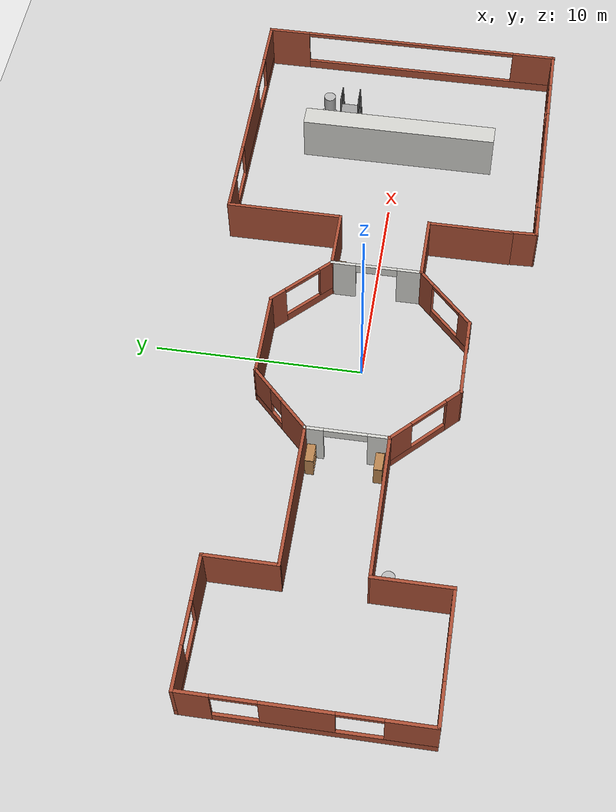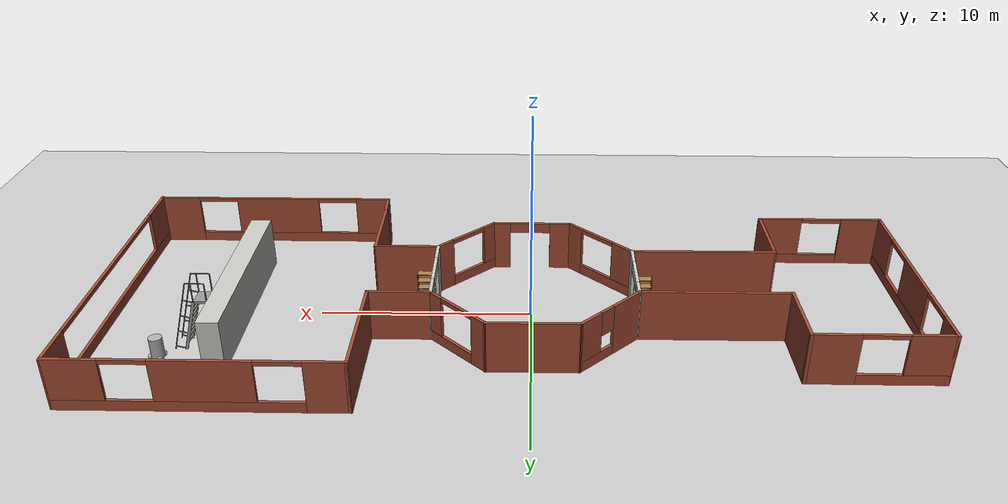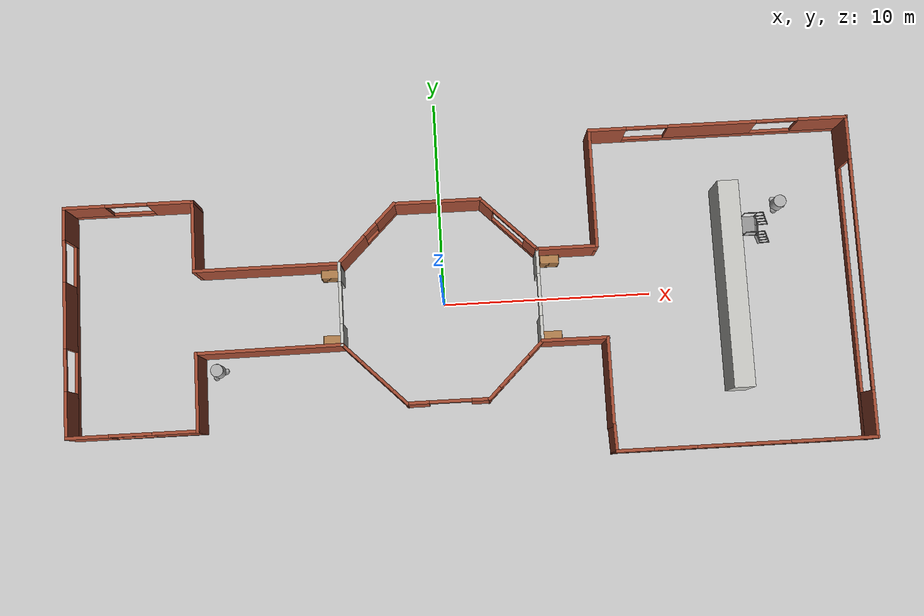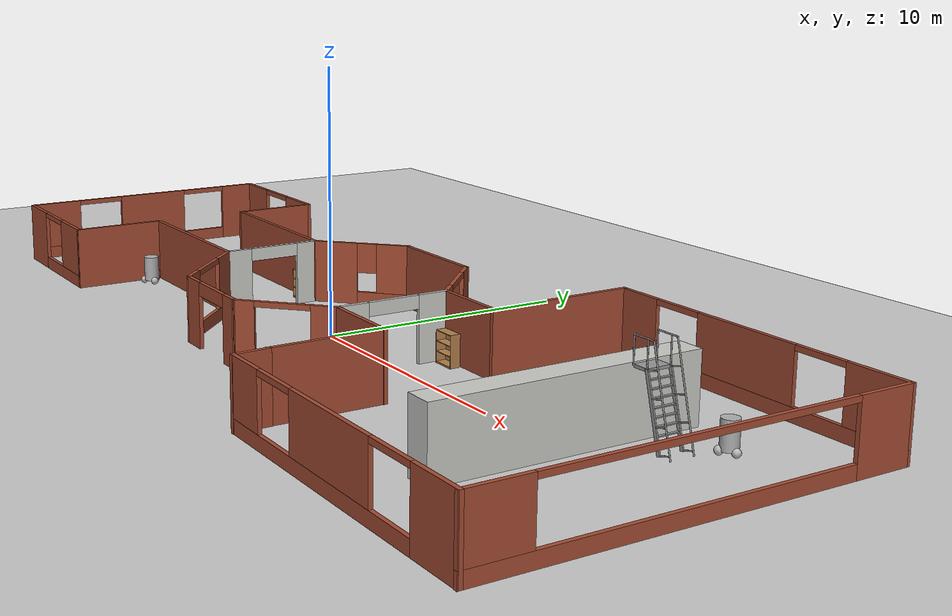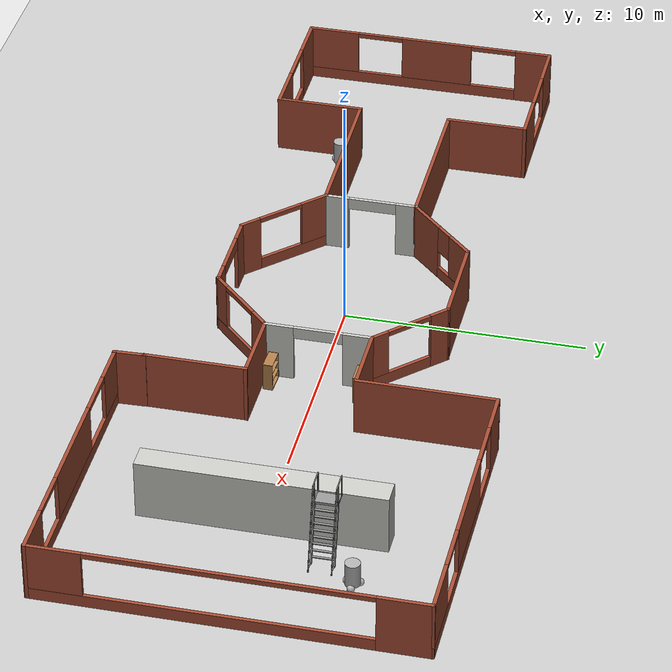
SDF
<sdf version="1.7">
 <world name="default">
  <light name="sun" type="directional">
   <pose>0 0 10 0 -0 0</pose>
   <diffuse>0.8 0.8 0.8 1</diffuse>
   <specular>0.2 0.2 0.2 1</specular>
   <attenuation>
    <range>1000</range>
    <constant>0.9</constant>
    <linear>0.01</linear>
    <quadratic>0.001</quadratic>
   </attenuation>
   <direction>-0.5 0.1 -0.9</direction>
   <spot><inner_angle>0</inner_angle><outer_angle>0</outer_angle><falloff>0</falloff></spot>
  </light>
  <model name="ground_plane">
   <static>1</static>
   <link name="link">
    <collision name="collision">
     <geometry><plane><normal>0 0 1</normal><size>100 100</size></plane></geometry>
     <surface>
      <contact><collide_bitmask>65535</collide_bitmask></contact>
      <friction><ode><mu>100</mu><mu2>50</mu2></ode></friction>
     </surface>
    </collision>
    <visual name="visual">
     <cast_shadows>0</cast_shadows>
     <geometry><plane><normal>0 0 1</normal><size>100 100</size></plane></geometry>
     <material>
      <script><uri>file://media/materials/scripts/gazebo.material</uri><name>Gazebo/Grey</name></script>
     </material>
    </visual>
   </link>
  </model>
  <gravity>0 0 -9.8</gravity>
  <magnetic_field>6e-06 2.3e-05 -4.2e-05</magnetic_field>
  <atmosphere type="adiabatic"/>
  <physics type="ode">
   <max_step_size>0.001</max_step_size>
   <real_time_factor>1</real_time_factor>
   <real_time_update_rate>1000</real_time_update_rate>
  </physics>
  <scene><ambient>0.4 0.4 0.4 1</ambient><background>0.7 0.7 0.7 1</background><shadows>1</shadows></scene>
  <spherical_coordinates>
   <surface_model>EARTH_WGS84</surface_model>
   <latitude_deg>0</latitude_deg>
   <longitude_deg>0</longitude_deg>
   <elevation>0</elevation>
   <heading_deg>0</heading_deg>
  </spherical_coordinates>
  <model name="Building">
   <pose>0.97548 0.086058 0 0 -0 0</pose>
   <link name="Wall_10">
    <pose>2.24078 -3.60079 0 0 0 -2.36445</pose>
    <visual name="Wall_10_Visual_0">
     <pose>-1.40328 0 1.25 0 -0 0</pose>
     <geometry><box><size>1.01679 0.15 2.5</size></box></geometry>
     <material>
      <script><uri>file://media/materials/scripts/gazebo.material</uri><name>Gazebo/Bricks</name></script>
      <ambient>0.760784 0.662745 0.627451 1</ambient>
     </material>
     <meta><layer>0</layer></meta>
    </visual>
    <collision name="Wall_10_Collision_0">
     <geometry><box><size>1.01679 0.15 2.5</size></box></geometry>
     <pose>-1.40328 0 1.25 0 -0 0</pose>
    </collision>
    <visual name="Wall_10_Visual_1">
     <pose>0.508396 0 0.25 0 -0 0</pose>
     <geometry><box><size>2.80656 0.15 0.5</size></box></geometry>
     <material>
      <script><uri>file://media/materials/scripts/gazebo.material</uri><name>Gazebo/Bricks</name></script>
      <ambient>0.760784 0.662745 0.627451 1</ambient>
     </material>
     <meta><layer>0</layer></meta>
    </visual>
    <collision name="Wall_10_Collision_1">
     <geometry><box><size>2.80656 0.15 0.5</size></box></geometry>
     <pose>0.508396 0 0.25 0 -0 0</pose>
    </collision>
    <visual name="Wall_10_Visual_2">
     <pose>1.5084 0 1.5 0 -0 0</pose>
     <geometry><box><size>0.806556 0.15 2</size></box></geometry>
     <material>
      <script><uri>file://media/materials/scripts/gazebo.material</uri><name>Gazebo/Bricks</name></script>
      <ambient>0.760784 0.662745 0.627451 1</ambient>
     </material>
     <meta><layer>0</layer></meta>
    </visual>
    <collision name="Wall_10_Collision_2">
     <geometry><box><size>0.806556 0.15 2</size></box></geometry>
     <pose>1.5084 0 1.5 0 -0 0</pose>
    </collision>
    <visual name="Wall_10_Visual_3">
     <pose>0.105118 0 2.4 0 -0 0</pose>
     <geometry><box><size>2 0.15 0.2</size></box></geometry>
     <material>
      <script><uri>file://media/materials/scripts/gazebo.material</uri><name>Gazebo/Bricks</name></script>
      <ambient>0.760784 0.662745 0.627451 1</ambient>
     </material>
     <meta><layer>0</layer></meta>
    </visual>
    <collision name="Wall_10_Collision_3">
     <geometry><box><size>2 0.15 0.2</size></box></geometry>
     <pose>0.105118 0 2.4 0 -0 0</pose>
    </collision>
   </link>
   <link name="Wall_12">
    <collision name="Wall_12_Collision">
     <geometry><box><size>7 0.15 2.5</size></box></geometry>
     <pose>0 0 1.25 0 -0 0</pose>
    </collision>
    <visual name="Wall_12_Visual">
     <pose>0 0 1.25 0 -0 0</pose>
     <geometry><box><size>7 0.15 2.5</size></box></geometry>
     <material>
      <script><uri>file://media/materials/scripts/gazebo.material</uri><name>Gazebo/Bricks</name></script>
      <ambient>0.760784 0.662745 0.627451 1</ambient>
     </material>
     <meta><layer>0</layer></meta>
    </visual>
    <pose>-9.24276 1.86039 0 0 -0 3.14159</pose>
   </link>
   <link name="Wall_13">
    <collision name="Wall_13_Collision">
     <geometry><box><size>3.5 0.15 2.5</size></box></geometry>
     <pose>0 0 1.25 0 -0 0</pose>
    </collision>
    <visual name="Wall_13_Visual">
     <pose>0 0 1.25 0 -0 0</pose>
     <geometry><box><size>3.5 0.15 2.5</size></box></geometry>
     <material>
      <script><uri>file://media/materials/scripts/gazebo.material</uri><name>Gazebo/Bricks</name></script>
      <ambient>0.760784 0.662745 0.627451 1</ambient>
     </material>
     <meta><layer>0</layer></meta>
    </visual>
    <pose>-12.6678 3.53539 0 0 -0 1.5708</pose>
   </link>
   <link name="Wall_14">
    <pose>-15.7178 5.21039 0 0 -0 3.14159</pose>
    <visual name="Wall_14_Visual_0">
     <pose>-2.01865 0 1.25 0 -0 0</pose>
     <geometry><box><size>2.2127 0.15 2.5</size></box></geometry>
     <material>
      <script><uri>file://media/materials/scripts/gazebo.material</uri><name>Gazebo/Bricks</name></script>
      <ambient>0.760784 0.662745 0.627451 1</ambient>
     </material>
     <meta><layer>0</layer></meta>
    </visual>
    <collision name="Wall_14_Collision_0">
     <geometry><box><size>2.2127 0.15 2.5</size></box></geometry>
     <pose>-2.01865 0 1.25 0 -0 0</pose>
    </collision>
    <visual name="Wall_14_Visual_1">
     <pose>1.10635 0 0.25 0 -0 0</pose>
     <geometry><box><size>4.0373 0.15 0.5</size></box></geometry>
     <material>
      <script><uri>file://media/materials/scripts/gazebo.material</uri><name>Gazebo/Bricks</name></script>
      <ambient>0.760784 0.662745 0.627451 1</ambient>
     </material>
     <meta><layer>0</layer></meta>
    </visual>
    <collision name="Wall_14_Collision_1">
     <geometry><box><size>4.0373 0.15 0.5</size></box></geometry>
     <pose>1.10635 0 0.25 0 -0 0</pose>
    </collision>
    <visual name="Wall_14_Visual_2">
     <pose>2.10635 0 1.5 0 -0 0</pose>
     <geometry><box><size>2.0373 0.15 2</size></box></geometry>
     <material>
      <script><uri>file://media/materials/scripts/gazebo.material</uri><name>Gazebo/Bricks</name></script>
      <ambient>0.760784 0.662745 0.627451 1</ambient>
     </material>
     <meta><layer>0</layer></meta>
    </visual>
    <collision name="Wall_14_Collision_2">
     <geometry><box><size>2.0373 0.15 2</size></box></geometry>
     <pose>2.10635 0 1.5 0 -0 0</pose>
    </collision>
    <visual name="Wall_14_Visual_3">
     <pose>0.0877 0 2.4 0 -0 0</pose>
     <geometry><box><size>2 0.15 0.2</size></box></geometry>
     <material>
      <script><uri>file://media/materials/scripts/gazebo.material</uri><name>Gazebo/Bricks</name></script>
      <ambient>0.760784 0.662745 0.627451 1</ambient>
     </material>
     <meta><layer>0</layer></meta>
    </visual>
    <collision name="Wall_14_Collision_3">
     <geometry><box><size>2 0.15 0.2</size></box></geometry>
     <pose>0.0877 0 2.4 0 -0 0</pose>
    </collision>
   </link>
   <link name="Wall_15">
    <pose>-18.7678 -0.214607 0 0 0 -1.5708</pose>
    <visual name="Wall_15_Visual_0">
     <pose>-4.69879 0 1.25 0 -0 0</pose>
     <geometry><box><size>1.60243 0.15 2.5</size></box></geometry>
     <material>
      <script><uri>file://media/materials/scripts/gazebo.material</uri><name>Gazebo/Bricks</name></script>
      <ambient>0.760784 0.662745 0.627451 1</ambient>
     </material>
     <meta><layer>0</layer></meta>
    </visual>
    <collision name="Wall_15_Collision_0">
     <geometry><box><size>1.60243 0.15 2.5</size></box></geometry>
     <pose>-4.69879 0 1.25 0 -0 0</pose>
    </collision>
    <visual name="Wall_15_Visual_1">
     <pose>0.801214 0 0.25 0 -0 0</pose>
     <geometry><box><size>9.39757 0.15 0.5</size></box></geometry>
     <material>
      <script><uri>file://media/materials/scripts/gazebo.material</uri><name>Gazebo/Bricks</name></script>
      <ambient>0.760784 0.662745 0.627451 1</ambient>
     </material>
     <meta><layer>0</layer></meta>
    </visual>
    <collision name="Wall_15_Collision_1">
     <geometry><box><size>9.39757 0.15 0.5</size></box></geometry>
     <pose>0.801214 0 0.25 0 -0 0</pose>
    </collision>
    <visual name="Wall_15_Visual_2">
     <pose>-0.326532 0 1.5 0 -0 0</pose>
     <geometry><box><size>3.14208 0.15 2</size></box></geometry>
     <material>
      <script><uri>file://media/materials/scripts/gazebo.material</uri><name>Gazebo/Bricks</name></script>
      <ambient>0.760784 0.662745 0.627451 1</ambient>
     </material>
     <meta><layer>0</layer></meta>
    </visual>
    <collision name="Wall_15_Collision_2">
     <geometry><box><size>3.14208 0.15 2</size></box></geometry>
     <pose>-0.326532 0 1.5 0 -0 0</pose>
    </collision>
    <visual name="Wall_15_Visual_3">
     <pose>4.37225 0 1.5 0 -0 0</pose>
     <geometry><box><size>2.25549 0.15 2</size></box></geometry>
     <material>
      <script><uri>file://media/materials/scripts/gazebo.material</uri><name>Gazebo/Bricks</name></script>
      <ambient>0.760784 0.662745 0.627451 1</ambient>
     </material>
     <meta><layer>0</layer></meta>
    </visual>
    <collision name="Wall_15_Collision_3">
     <geometry><box><size>2.25549 0.15 2</size></box></geometry>
     <pose>4.37225 0 1.5 0 -0 0</pose>
    </collision>
    <visual name="Wall_15_Visual_4">
     <pose>-2.89757 0 2.4 0 -0 0</pose>
     <geometry><box><size>2 0.15 0.2</size></box></geometry>
     <material>
      <script><uri>file://media/materials/scripts/gazebo.material</uri><name>Gazebo/Bricks</name></script>
      <ambient>0.760784 0.662745 0.627451 1</ambient>
     </material>
     <meta><layer>0</layer></meta>
    </visual>
    <collision name="Wall_15_Collision_4">
     <geometry><box><size>2 0.15 0.2</size></box></geometry>
     <pose>-2.89757 0 2.4 0 -0 0</pose>
    </collision>
    <visual name="Wall_15_Visual_5">
     <pose>2.24451 0 2.4 0 -0 0</pose>
     <geometry><box><size>2 0.15 0.2</size></box></geometry>
     <material>
      <script><uri>file://media/materials/scripts/gazebo.material</uri><name>Gazebo/Bricks</name></script>
      <ambient>0.760784 0.662745 0.627451 1</ambient>
     </material>
     <meta><layer>0</layer></meta>
    </visual>
    <collision name="Wall_15_Collision_5">
     <geometry><box><size>2 0.15 0.2</size></box></geometry>
     <pose>2.24451 0 2.4 0 -0 0</pose>
    </collision>
   </link>
   <link name="Wall_16">
    <pose>-15.7178 -5.63961 0 0 -0 0</pose>
    <visual name="Wall_16_Visual_0">
     <pose>-2.10635 0 1.25 0 -0 0</pose>
     <geometry><box><size>2.0373 0.15 2.5</size></box></geometry>
     <material>
      <script><uri>file://media/materials/scripts/gazebo.material</uri><name>Gazebo/Bricks</name></script>
      <ambient>0.760784 0.662745 0.627451 1</ambient>
     </material>
     <meta><layer>0</layer></meta>
    </visual>
    <collision name="Wall_16_Collision_0">
     <geometry><box><size>2.0373 0.15 2.5</size></box></geometry>
     <pose>-2.10635 0 1.25 0 -0 0</pose>
    </collision>
    <visual name="Wall_16_Visual_1">
     <pose>1.01865 0 0.25 0 -0 0</pose>
     <geometry><box><size>4.2127 0.15 0.5</size></box></geometry>
     <material>
      <script><uri>file://media/materials/scripts/gazebo.material</uri><name>Gazebo/Bricks</name></script>
      <ambient>0.760784 0.662745 0.627451 1</ambient>
     </material>
     <meta><layer>0</layer></meta>
    </visual>
    <collision name="Wall_16_Collision_1">
     <geometry><box><size>4.2127 0.15 0.5</size></box></geometry>
     <pose>1.01865 0 0.25 0 -0 0</pose>
    </collision>
    <visual name="Wall_16_Visual_2">
     <pose>2.01865 0 1.5 0 -0 0</pose>
     <geometry><box><size>2.2127 0.15 2</size></box></geometry>
     <material>
      <script><uri>file://media/materials/scripts/gazebo.material</uri><name>Gazebo/Bricks</name></script>
      <ambient>0.760784 0.662745 0.627451 1</ambient>
     </material>
     <meta><layer>0</layer></meta>
    </visual>
    <collision name="Wall_16_Collision_2">
     <geometry><box><size>2.2127 0.15 2</size></box></geometry>
     <pose>2.01865 0 1.5 0 -0 0</pose>
    </collision>
    <visual name="Wall_16_Visual_3">
     <pose>-0.0877 0 2.4 0 -0 0</pose>
     <geometry><box><size>2 0.15 0.2</size></box></geometry>
     <material>
      <script><uri>file://media/materials/scripts/gazebo.material</uri><name>Gazebo/Bricks</name></script>
      <ambient>0.760784 0.662745 0.627451 1</ambient>
     </material>
     <meta><layer>0</layer></meta>
    </visual>
    <collision name="Wall_16_Collision_3">
     <geometry><box><size>2 0.15 0.2</size></box></geometry>
     <pose>-0.0877 0 2.4 0 -0 0</pose>
    </collision>
   </link>
   <link name="Wall_17">
    <collision name="Wall_17_Collision">
     <geometry><box><size>3.75 0.15 2.5</size></box></geometry>
     <pose>0 0 1.25 0 -0 0</pose>
    </collision>
    <visual name="Wall_17_Visual">
     <pose>0 0 1.25 0 -0 0</pose>
     <geometry><box><size>3.75 0.15 2.5</size></box></geometry>
     <material>
      <script><uri>file://media/materials/scripts/gazebo.material</uri><name>Gazebo/Bricks</name></script>
      <ambient>0.760784 0.662745 0.627451 1</ambient>
     </material>
     <meta><layer>0</layer></meta>
    </visual>
    <pose>-12.6678 -3.83961 0 0 -0 1.5708</pose>
   </link>
   <link name="Wall_18">
    <collision name="Wall_18_Collision">
     <geometry><box><size>7.00018 0.15 2.5</size></box></geometry>
     <pose>0 0 1.25 0 -0 0</pose>
    </collision>
    <visual name="Wall_18_Visual">
     <pose>0 0 1.25 0 -0 0</pose>
     <geometry><box><size>7.00018 0.15 2.5</size></box></geometry>
     <material>
      <script><uri>file://media/materials/scripts/gazebo.material</uri><name>Gazebo/Bricks</name></script>
      <ambient>0.760784 0.662745 0.627451 1</ambient>
     </material>
     <meta><layer>0</layer></meta>
    </visual>
    <pose>-9.24276 -2.01461 0 0 -0 0.007299</pose>
   </link>
   <link name="Wall_20">
    <collision name="Wall_20_Collision">
     <geometry><box><size>3 0.15 2.5</size></box></geometry>
     <pose>0 0 1.25 0 -0 0</pose>
    </collision>
    <visual name="Wall_20_Visual">
     <pose>0 0 1.25 0 -0 0</pose>
     <geometry><box><size>3 0.15 2.5</size></box></geometry>
     <material>
      <script><uri>file://media/materials/scripts/gazebo.material</uri><name>Gazebo/Bricks</name></script>
      <ambient>0.760784 0.662745 0.627451 1</ambient>
     </material>
     <meta><layer>0</layer></meta>
    </visual>
    <pose>4.97519 2.03717 0 0 -0 0</pose>
   </link>
   <link name="Wall_21">
    <collision name="Wall_21_Collision">
     <geometry><box><size>5.75 0.15 2.5</size></box></geometry>
     <pose>0 0 1.25 0 -0 0</pose>
    </collision>
    <visual name="Wall_21_Visual">
     <pose>0 0 1.25 0 -0 0</pose>
     <geometry><box><size>5.75 0.15 2.5</size></box></geometry>
     <material>
      <script><uri>file://media/materials/scripts/gazebo.material</uri><name>Gazebo/Bricks</name></script>
      <ambient>0.760784 0.662745 0.627451 1</ambient>
     </material>
     <meta><layer>0</layer></meta>
    </visual>
    <pose>6.40019 4.83717 0 0 -0 1.5708</pose>
   </link>
   <link name="Wall_22">
    <pose>12.5752 7.63717 0 0 -0 0</pose>
    <visual name="Wall_22_Visual_0">
     <pose>-5.31867 0 1.25 0 -0 0</pose>
     <geometry><box><size>1.86265 0.15 2.5</size></box></geometry>
     <material>
      <script><uri>file://media/materials/scripts/gazebo.material</uri><name>Gazebo/Bricks</name></script>
      <ambient>0.760784 0.662745 0.627451 1</ambient>
     </material>
     <meta><layer>0</layer></meta>
    </visual>
    <collision name="Wall_22_Collision_0">
     <geometry><box><size>1.86265 0.15 2.5</size></box></geometry>
     <pose>-5.31867 0 1.25 0 -0 0</pose>
    </collision>
    <visual name="Wall_22_Visual_1">
     <pose>0.931327 0 0.25 0 -0 0</pose>
     <geometry><box><size>10.6373 0.15 0.5</size></box></geometry>
     <material>
      <script><uri>file://media/materials/scripts/gazebo.material</uri><name>Gazebo/Bricks</name></script>
      <ambient>0.760784 0.662745 0.627451 1</ambient>
     </material>
     <meta><layer>0</layer></meta>
    </visual>
    <collision name="Wall_22_Collision_1">
     <geometry><box><size>10.6373 0.15 0.5</size></box></geometry>
     <pose>0.931327 0 0.25 0 -0 0</pose>
    </collision>
    <visual name="Wall_22_Visual_2">
     <pose>-0.256624 0 1.5 0 -0 0</pose>
     <geometry><box><size>4.26144 0.15 2</size></box></geometry>
     <material>
      <script><uri>file://media/materials/scripts/gazebo.material</uri><name>Gazebo/Bricks</name></script>
      <ambient>0.760784 0.662745 0.627451 1</ambient>
     </material>
     <meta><layer>0</layer></meta>
    </visual>
    <collision name="Wall_22_Collision_2">
     <geometry><box><size>4.26144 0.15 2</size></box></geometry>
     <pose>-0.256624 0 1.5 0 -0 0</pose>
    </collision>
    <visual name="Wall_22_Visual_3">
     <pose>5.06205 0 1.5 0 -0 0</pose>
     <geometry><box><size>2.3759 0.15 2</size></box></geometry>
     <material>
      <script><uri>file://media/materials/scripts/gazebo.material</uri><name>Gazebo/Bricks</name></script>
      <ambient>0.760784 0.662745 0.627451 1</ambient>
     </material>
     <meta><layer>0</layer></meta>
    </visual>
    <collision name="Wall_22_Collision_3">
     <geometry><box><size>2.3759 0.15 2</size></box></geometry>
     <pose>5.06205 0 1.5 0 -0 0</pose>
    </collision>
    <visual name="Wall_22_Visual_4">
     <pose>-3.38734 0 2.4 0 -0 0</pose>
     <geometry><box><size>2 0.15 0.2</size></box></geometry>
     <material>
      <script><uri>file://media/materials/scripts/gazebo.material</uri><name>Gazebo/Bricks</name></script>
      <ambient>0.760784 0.662745 0.627451 1</ambient>
     </material>
     <meta><layer>0</layer></meta>
    </visual>
    <collision name="Wall_22_Collision_4">
     <geometry><box><size>2 0.15 0.2</size></box></geometry>
     <pose>-3.38734 0 2.4 0 -0 0</pose>
    </collision>
    <visual name="Wall_22_Visual_5">
     <pose>2.8741 0 2.4 0 -0 0</pose>
     <geometry><box><size>2 0.15 0.2</size></box></geometry>
     <material>
      <script><uri>file://media/materials/scripts/gazebo.material</uri><name>Gazebo/Bricks</name></script>
      <ambient>0.760784 0.662745 0.627451 1</ambient>
     </material>
     <meta><layer>0</layer></meta>
    </visual>
    <collision name="Wall_22_Collision_5">
     <geometry><box><size>2 0.15 0.2</size></box></geometry>
     <pose>2.8741 0 2.4 0 -0 0</pose>
    </collision>
   </link>
   <link name="Wall_23">
    <pose>18.7589 0.001252 0 0 0 -1.56965</pose>
    <visual name="Wall_23_Visual_0">
     <pose>-6.62578 0 1.25 0 -0 0</pose>
     <geometry><box><size>2.17028 0.15 2.5</size></box></geometry>
     <material>
      <script><uri>file://media/materials/scripts/gazebo.material</uri><name>Gazebo/Bricks</name></script>
      <ambient>0.760784 0.662745 0.627451 1</ambient>
     </material>
     <meta><layer>0</layer></meta>
    </visual>
    <collision name="Wall_23_Collision_0">
     <geometry><box><size>2.17028 0.15 2.5</size></box></geometry>
     <pose>-6.62578 0 1.25 0 -0 0</pose>
    </collision>
    <visual name="Wall_23_Visual_1">
     <pose>1.08514 0 0.25 0 -0 0</pose>
     <geometry><box><size>13.2516 0.15 0.5</size></box></geometry>
     <material>
      <script><uri>file://media/materials/scripts/gazebo.material</uri><name>Gazebo/Bricks</name></script>
      <ambient>0.760784 0.662745 0.627451 1</ambient>
     </material>
     <meta><layer>0</layer></meta>
    </visual>
    <collision name="Wall_23_Collision_1">
     <geometry><box><size>13.2516 0.15 0.5</size></box></geometry>
     <pose>1.08514 0 0.25 0 -0 0</pose>
    </collision>
    <visual name="Wall_23_Visual_2">
     <pose>6.58514 0 1.5 0 -0 0</pose>
     <geometry><box><size>2.25156 0.15 2</size></box></geometry>
     <material>
      <script><uri>file://media/materials/scripts/gazebo.material</uri><name>Gazebo/Bricks</name></script>
      <ambient>0.760784 0.662745 0.627451 1</ambient>
     </material>
     <meta><layer>0</layer></meta>
    </visual>
    <collision name="Wall_23_Collision_2">
     <geometry><box><size>2.25156 0.15 2</size></box></geometry>
     <pose>6.58514 0 1.5 0 -0 0</pose>
    </collision>
    <visual name="Wall_23_Visual_3">
     <pose>-0.040637 0 2.4 0 -0 0</pose>
     <geometry><box><size>11 0.15 0.2</size></box></geometry>
     <material>
      <script><uri>file://media/materials/scripts/gazebo.material</uri><name>Gazebo/Bricks</name></script>
      <ambient>0.760784 0.662745 0.627451 1</ambient>
     </material>
     <meta><layer>0</layer></meta>
    </visual>
    <collision name="Wall_23_Collision_3">
     <geometry><box><size>11 0.15 0.2</size></box></geometry>
     <pose>-0.040637 0 2.4 0 -0 0</pose>
    </collision>
   </link>
   <link name="Wall_24">
    <pose>12.7177 -7.61717 0 0 -0 3.14159</pose>
    <visual name="Wall_24_Visual_0">
     <pose>-5.07697 0 1.25 0 -0 0</pose>
     <geometry><box><size>2.09606 0.15 2.5</size></box></geometry>
     <material>
      <script><uri>file://media/materials/scripts/gazebo.material</uri><name>Gazebo/Bricks</name></script>
      <ambient>0.760784 0.662745 0.627451 1</ambient>
     </material>
     <meta><layer>0</layer></meta>
    </visual>
    <collision name="Wall_24_Collision_0">
     <geometry><box><size>2.09606 0.15 2.5</size></box></geometry>
     <pose>-5.07697 0 1.25 0 -0 0</pose>
    </collision>
    <visual name="Wall_24_Visual_1">
     <pose>1.04803 0 0.25 0 -0 0</pose>
     <geometry><box><size>10.1539 0.15 0.5</size></box></geometry>
     <material>
      <script><uri>file://media/materials/scripts/gazebo.material</uri><name>Gazebo/Bricks</name></script>
      <ambient>0.760784 0.662745 0.627451 1</ambient>
     </material>
     <meta><layer>0</layer></meta>
    </visual>
    <collision name="Wall_24_Collision_1">
     <geometry><box><size>10.1539 0.15 0.5</size></box></geometry>
     <pose>1.04803 0 0.25 0 -0 0</pose>
    </collision>
    <visual name="Wall_24_Visual_2">
     <pose>0.154253 0 1.5 0 -0 0</pose>
     <geometry><box><size>4.36638 0.15 2</size></box></geometry>
     <material>
      <script><uri>file://media/materials/scripts/gazebo.material</uri><name>Gazebo/Bricks</name></script>
      <ambient>0.760784 0.662745 0.627451 1</ambient>
     </material>
     <meta><layer>0</layer></meta>
    </visual>
    <collision name="Wall_24_Collision_2">
     <geometry><box><size>4.36638 0.15 2</size></box></geometry>
     <pose>0.154253 0 1.5 0 -0 0</pose>
    </collision>
    <visual name="Wall_24_Visual_3">
     <pose>5.23122 0 1.5 0 -0 0</pose>
     <geometry><box><size>1.78756 0.15 2</size></box></geometry>
     <material>
      <script><uri>file://media/materials/scripts/gazebo.material</uri><name>Gazebo/Bricks</name></script>
      <ambient>0.760784 0.662745 0.627451 1</ambient>
     </material>
     <meta><layer>0</layer></meta>
    </visual>
    <collision name="Wall_24_Collision_3">
     <geometry><box><size>1.78756 0.15 2</size></box></geometry>
     <pose>5.23122 0 1.5 0 -0 0</pose>
    </collision>
    <visual name="Wall_24_Visual_4">
     <pose>-3.02894 0 2.4 0 -0 0</pose>
     <geometry><box><size>2 0.15 0.2</size></box></geometry>
     <material>
      <script><uri>file://media/materials/scripts/gazebo.material</uri><name>Gazebo/Bricks</name></script>
      <ambient>0.760784 0.662745 0.627451 1</ambient>
     </material>
     <meta><layer>0</layer></meta>
    </visual>
    <collision name="Wall_24_Collision_4">
     <geometry><box><size>2 0.15 0.2</size></box></geometry>
     <pose>-3.02894 0 2.4 0 -0 0</pose>
    </collision>
    <visual name="Wall_24_Visual_5">
     <pose>3.33745 0 2.4 0 -0 0</pose>
     <geometry><box><size>2 0.15 0.2</size></box></geometry>
     <material>
      <script><uri>file://media/materials/scripts/gazebo.material</uri><name>Gazebo/Bricks</name></script>
      <ambient>0.760784 0.662745 0.627451 1</ambient>
     </material>
     <meta><layer>0</layer></meta>
    </visual>
    <collision name="Wall_24_Collision_5">
     <geometry><box><size>2 0.15 0.2</size></box></geometry>
     <pose>3.33745 0 2.4 0 -0 0</pose>
    </collision>
   </link>
   <link name="Wall_25">
    <collision name="Wall_25_Collision">
     <geometry><box><size>1.35756 0.15 2.5</size></box></geometry>
     <pose>0 0 1.25 0 -0 0</pose>
    </collision>
    <visual name="Wall_25_Visual">
     <pose>0 0 1.25 0 -0 0</pose>
     <geometry><box><size>1.35756 0.15 2.5</size></box></geometry>
     <material>
      <script><uri>file://media/materials/scripts/gazebo.material</uri><name>Gazebo/Bricks</name></script>
      <ambient>1 1 1 1</ambient>
     </material>
     <meta><layer>0</layer></meta>
    </visual>
    <pose>6.64644 -7.03126 0 0 -0 1.60597</pose>
   </link>
   <link name="Wall_26">
    <collision name="Wall_26_Collision">
     <geometry><box><size>4.25 0.15 2.5</size></box></geometry>
     <pose>0 0 1.25 0 -0 0</pose>
    </collision>
    <visual name="Wall_26_Visual">
     <pose>0 0 1.25 0 -0 0</pose>
     <geometry><box><size>4.25 0.15 2.5</size></box></geometry>
     <material>
      <script><uri>file://media/materials/scripts/gazebo.material</uri><name>Gazebo/Bricks</name></script>
      <ambient>0.760784 0.662745 0.627451 1</ambient>
     </material>
     <meta><layer>0</layer></meta>
    </visual>
    <pose>6.60772 -4.37785 0 0 -0 1.5708</pose>
   </link>
   <link name="Wall_27">
    <collision name="Wall_27_Collision">
     <geometry><box><size>3.22506 0.15 2.5</size></box></geometry>
     <pose>0 0 1.25 0 -0 0</pose>
    </collision>
    <visual name="Wall_27_Visual">
     <pose>0 0 1.25 0 -0 0</pose>
     <geometry><box><size>3.22506 0.15 2.5</size></box></geometry>
     <material>
      <script><uri>file://media/materials/scripts/gazebo.material</uri><name>Gazebo/Bricks</name></script>
      <ambient>0.760784 0.662745 0.627451 1</ambient>
     </material>
     <meta><layer>0</layer></meta>
    </visual>
    <pose>5.0877 -2.32034 0 0 -0 3.13671</pose>
   </link>
   <link name="Wall_29">
    <collision name="Wall_29_Collision">
     <geometry><box><size>9.85029 1 2.5</size></box></geometry>
     <pose>0 0 1.25 0 -0 0</pose>
    </collision>
    <visual name="Wall_29_Visual">
     <pose>0 0 1.25 0 -0 0</pose>
     <geometry><box><size>9.85029 1 2.5</size></box></geometry>
     <material>
      <script><uri>file://media/materials/scripts/gazebo.material</uri><name>Gazebo/CeilingTiled</name></script>
      <ambient>1 1 1 1</ambient>
     </material>
     <meta><layer>0</layer></meta>
    </visual>
    <pose>12.8254 -0.080745 0 0 -0 1.5708</pose>
   </link>
   <link name="Wall_3">
    <pose>-0.993622 -4.88875 0 0 -0 3.14159</pose>
    <visual name="Wall_3_Visual_0">
     <pose>-1.54485 0 1.25 0 -0 0</pose>
     <geometry><box><size>0.910304 0.15 2.5</size></box></geometry>
     <material>
      <script><uri>file://media/materials/scripts/gazebo.material</uri><name>Gazebo/Bricks</name></script>
      <ambient>0.760784 0.662745 0.627451 1</ambient>
     </material>
     <meta><layer>0</layer></meta>
    </visual>
    <collision name="Wall_3_Collision_0">
     <geometry><box><size>0.910304 0.15 2.5</size></box></geometry>
     <pose>-1.54485 0 1.25 0 -0 0</pose>
    </collision>
    <visual name="Wall_3_Visual_1">
     <pose>1.45515 0 1.25 0 -0 0</pose>
     <geometry><box><size>1.0897 0.15 2.5</size></box></geometry>
     <material>
      <script><uri>file://media/materials/scripts/gazebo.material</uri><name>Gazebo/Bricks</name></script>
      <ambient>0.760784 0.662745 0.627451 1</ambient>
     </material>
     <meta><layer>0</layer></meta>
    </visual>
    <collision name="Wall_3_Collision_1">
     <geometry><box><size>1.0897 0.15 2.5</size></box></geometry>
     <pose>1.45515 0 1.25 0 -0 0</pose>
    </collision>
    <visual name="Wall_3_Visual_2">
     <pose>-0.089696 0 2.25 0 -0 0</pose>
     <geometry><box><size>2 0.15 0.5</size></box></geometry>
     <material>
      <script><uri>file://media/materials/scripts/gazebo.material</uri><name>Gazebo/Bricks</name></script>
      <ambient>0.760784 0.662745 0.627451 1</ambient>
     </material>
     <meta><layer>0</layer></meta>
    </visual>
    <collision name="Wall_3_Collision_2">
     <geometry><box><size>2 0.15 0.5</size></box></geometry>
     <pose>-0.089696 0 2.25 0 -0 0</pose>
    </collision>
   </link>
   <link name="Wall_4">
    <pose>-4.36819 -3.43918 0 0 -0 2.35619</pose>
    <visual name="Wall_4_Visual_0">
     <pose>-1.64929 0 1.25 0 -0 0</pose>
     <geometry><box><size>0.951423 0.15 2.5</size></box></geometry>
     <material>
      <script><uri>file://media/materials/scripts/gazebo.material</uri><name>Gazebo/Bricks</name></script>
      <ambient>0.760784 0.662745 0.627451 1</ambient>
     </material>
     <meta><layer>0</layer></meta>
    </visual>
    <collision name="Wall_4_Collision_0">
     <geometry><box><size>0.951423 0.15 2.5</size></box></geometry>
     <pose>-1.64929 0 1.25 0 -0 0</pose>
    </collision>
    <visual name="Wall_4_Visual_1">
     <pose>0.475711 0 0.25 0 -0 0</pose>
     <geometry><box><size>3.29858 0.15 0.5</size></box></geometry>
     <material>
      <script><uri>file://media/materials/scripts/gazebo.material</uri><name>Gazebo/Bricks</name></script>
      <ambient>0.760784 0.662745 0.627451 1</ambient>
     </material>
     <meta><layer>0</layer></meta>
    </visual>
    <collision name="Wall_4_Collision_1">
     <geometry><box><size>3.29858 0.15 0.5</size></box></geometry>
     <pose>0.475711 0 0.25 0 -0 0</pose>
    </collision>
    <visual name="Wall_4_Visual_2">
     <pose>1.47571 0 1.5 0 -0 0</pose>
     <geometry><box><size>1.29858 0.15 2</size></box></geometry>
     <material>
      <script><uri>file://media/materials/scripts/gazebo.material</uri><name>Gazebo/Bricks</name></script>
      <ambient>0.760784 0.662745 0.627451 1</ambient>
     </material>
     <meta><layer>0</layer></meta>
    </visual>
    <collision name="Wall_4_Collision_2">
     <geometry><box><size>1.29858 0.15 2</size></box></geometry>
     <pose>1.47571 0 1.5 0 -0 0</pose>
    </collision>
    <visual name="Wall_4_Visual_3">
     <pose>-0.173577 0 2.4 0 -0 0</pose>
     <geometry><box><size>2 0.15 0.2</size></box></geometry>
     <material>
      <script><uri>file://media/materials/scripts/gazebo.material</uri><name>Gazebo/Bricks</name></script>
      <ambient>0.760784 0.662745 0.627451 1</ambient>
     </material>
     <meta><layer>0</layer></meta>
    </visual>
    <collision name="Wall_4_Collision_3">
     <geometry><box><size>2 0.15 0.2</size></box></geometry>
     <pose>-0.173577 0 2.4 0 -0 0</pose>
    </collision>
   </link>
   <link name="Wall_5">
    <pose>-5.81776 -0.064607 0 0 -0 1.5708</pose>
    <visual name="Wall_5_Visual_0">
     <pose>-1.4642 0 1.25 0 -0 0</pose>
     <geometry><box><size>1.07159 0.15 2.5</size></box></geometry>
     <material>
      <script><uri>file://media/materials/scripts/gazebo.material</uri><name>Gazebo/CeilingTiled</name></script>
      <ambient>1 1 1 1</ambient>
     </material>
     <meta><layer>0</layer></meta>
    </visual>
    <collision name="Wall_5_Collision_0">
     <geometry><box><size>1.07159 0.15 2.5</size></box></geometry>
     <pose>-1.4642 0 1.25 0 -0 0</pose>
    </collision>
    <visual name="Wall_5_Visual_1">
     <pose>1.5358 0 1.25 0 -0 0</pose>
     <geometry><box><size>0.928408 0.15 2.5</size></box></geometry>
     <material>
      <script><uri>file://media/materials/scripts/gazebo.material</uri><name>Gazebo/CeilingTiled</name></script>
      <ambient>1 1 1 1</ambient>
     </material>
     <meta><layer>0</layer></meta>
    </visual>
    <collision name="Wall_5_Collision_1">
     <geometry><box><size>0.928408 0.15 2.5</size></box></geometry>
     <pose>1.5358 0 1.25 0 -0 0</pose>
    </collision>
    <visual name="Wall_5_Visual_2">
     <pose>0.071592 0 2.25 0 -0 0</pose>
     <geometry><box><size>2 0.15 0.5</size></box></geometry>
     <material>
      <script><uri>file://media/materials/scripts/gazebo.material</uri><name>Gazebo/CeilingTiled</name></script>
      <ambient>1 1 1 1</ambient>
     </material>
     <meta><layer>0</layer></meta>
    </visual>
    <collision name="Wall_5_Collision_2">
     <geometry><box><size>2 0.15 0.5</size></box></geometry>
     <pose>0.071592 0 2.25 0 -0 0</pose>
    </collision>
   </link>
   <link name="Wall_6">
    <pose>-4.45658 3.22157 0 0 -0 0.785398</pose>
    <visual name="Wall_6_Visual_0">
     <pose>-1.07429 0 1.25 0 -0 0</pose>
     <geometry><box><size>1.85142 0.15 2.5</size></box></geometry>
     <material>
      <script><uri>file://media/materials/scripts/gazebo.material</uri><name>Gazebo/Bricks</name></script>
      <ambient>0.760784 0.662745 0.627451 1</ambient>
     </material>
     <meta><layer>0</layer></meta>
    </visual>
    <collision name="Wall_6_Collision_0">
     <geometry><box><size>1.85142 0.15 2.5</size></box></geometry>
     <pose>-1.07429 0 1.25 0 -0 0</pose>
    </collision>
    <visual name="Wall_6_Visual_1">
     <pose>0.925708 0 0.25 0 -0 0</pose>
     <geometry><box><size>2.14859 0.15 0.5</size></box></geometry>
     <material>
      <script><uri>file://media/materials/scripts/gazebo.material</uri><name>Gazebo/Bricks</name></script>
      <ambient>0.760784 0.662745 0.627451 1</ambient>
     </material>
     <meta><layer>0</layer></meta>
    </visual>
    <collision name="Wall_6_Collision_1">
     <geometry><box><size>2.14859 0.15 0.5</size></box></geometry>
     <pose>0.925708 0 0.25 0 -0 0</pose>
    </collision>
    <visual name="Wall_6_Visual_2">
     <pose>1.32571 0 1.5 0 -0 0</pose>
     <geometry><box><size>1.34858 0.15 2</size></box></geometry>
     <material>
      <script><uri>file://media/materials/scripts/gazebo.material</uri><name>Gazebo/Bricks</name></script>
      <ambient>0.760784 0.662745 0.627451 1</ambient>
     </material>
     <meta><layer>0</layer></meta>
    </visual>
    <collision name="Wall_6_Collision_2">
     <geometry><box><size>1.34858 0.15 2</size></box></geometry>
     <pose>1.32571 0 1.5 0 -0 0</pose>
    </collision>
    <visual name="Wall_6_Visual_3">
     <pose>0.251415 0 1.9 0 -0 0</pose>
     <geometry><box><size>0.8 0.15 1.2</size></box></geometry>
     <material>
      <script><uri>file://media/materials/scripts/gazebo.material</uri><name>Gazebo/Bricks</name></script>
      <ambient>0.760784 0.662745 0.627451 1</ambient>
     </material>
     <meta><layer>0</layer></meta>
    </visual>
    <collision name="Wall_6_Collision_3">
     <geometry><box><size>0.8 0.15 1.2</size></box></geometry>
     <pose>0.251415 0 1.9 0 -0 0</pose>
    </collision>
   </link>
   <link name="Wall_7">
    <collision name="Wall_7_Collision">
     <geometry><box><size>4.25 0.15 2.5</size></box></geometry>
     <pose>0 0 1.25 0 -0 0</pose>
    </collision>
    <visual name="Wall_7_Visual">
     <pose>0 0 1.25 0 -0 0</pose>
     <geometry><box><size>4.25 0.15 2.5</size></box></geometry>
     <material>
      <script><uri>file://media/materials/scripts/gazebo.material</uri><name>Gazebo/Bricks</name></script>
      <ambient>0.760784 0.662745 0.627451 1</ambient>
     </material>
     <meta><layer>0</layer></meta>
    </visual>
    <pose>-1.0454 4.58275 0 0 -0 0</pose>
   </link>
   <link name="Wall_8">
    <pose>2.27739 3.30996 0 0 0 -0.785398</pose>
    <visual name="Wall_8_Visual_0">
     <pose>-1.41922 0 1.25 0 -0 0</pose>
     <geometry><box><size>0.911556 0.15 2.5</size></box></geometry>
     <material>
      <script><uri>file://media/materials/scripts/gazebo.material</uri><name>Gazebo/Bricks</name></script>
      <ambient>0.760784 0.662745 0.627451 1</ambient>
     </material>
     <meta><layer>0</layer></meta>
    </visual>
    <collision name="Wall_8_Collision_0">
     <geometry><box><size>0.911556 0.15 2.5</size></box></geometry>
     <pose>-1.41922 0 1.25 0 -0 0</pose>
    </collision>
    <visual name="Wall_8_Visual_1">
     <pose>0.455778 0 0.25 0 -0 0</pose>
     <geometry><box><size>2.83844 0.15 0.5</size></box></geometry>
     <material>
      <script><uri>file://media/materials/scripts/gazebo.material</uri><name>Gazebo/Bricks</name></script>
      <ambient>0.760784 0.662745 0.627451 1</ambient>
     </material>
     <meta><layer>0</layer></meta>
    </visual>
    <collision name="Wall_8_Collision_1">
     <geometry><box><size>2.83844 0.15 0.5</size></box></geometry>
     <pose>0.455778 0 0.25 0 -0 0</pose>
    </collision>
    <visual name="Wall_8_Visual_2">
     <pose>1.45578 0 1.5 0 -0 0</pose>
     <geometry><box><size>0.838444 0.15 2</size></box></geometry>
     <material>
      <script><uri>file://media/materials/scripts/gazebo.material</uri><name>Gazebo/Bricks</name></script>
      <ambient>0.760784 0.662745 0.627451 1</ambient>
     </material>
     <meta><layer>0</layer></meta>
    </visual>
    <collision name="Wall_8_Collision_2">
     <geometry><box><size>0.838444 0.15 2</size></box></geometry>
     <pose>1.45578 0 1.5 0 -0 0</pose>
    </collision>
    <visual name="Wall_8_Visual_3">
     <pose>0.036556 0 2.4 0 -0 0</pose>
     <geometry><box><size>2 0.15 0.2</size></box></geometry>
     <material>
      <script><uri>file://media/materials/scripts/gazebo.material</uri><name>Gazebo/Bricks</name></script>
      <ambient>0.760784 0.662745 0.627451 1</ambient>
     </material>
     <meta><layer>0</layer></meta>
    </visual>
    <collision name="Wall_8_Collision_3">
     <geometry><box><size>2 0.15 0.2</size></box></geometry>
     <pose>0.036556 0 2.4 0 -0 0</pose>
    </collision>
   </link>
   <link name="Wall_9">
    <pose>3.55019 -0.13783 0 0 0 -1.5708</pose>
    <visual name="Wall_9_Visual_0">
     <pose>-1.62745 0 1.25 0 -0 0</pose>
     <geometry><box><size>1.2451 0.15 2.5</size></box></geometry>
     <material>
      <script><uri>file://media/materials/scripts/gazebo.material</uri><name>Gazebo/CeilingTiled</name></script>
      <ambient>1 1 1 1</ambient>
     </material>
     <meta><layer>0</layer></meta>
    </visual>
    <collision name="Wall_9_Collision_0">
     <geometry><box><size>1.2451 0.15 2.5</size></box></geometry>
     <pose>-1.62745 0 1.25 0 -0 0</pose>
    </collision>
    <visual name="Wall_9_Visual_1">
     <pose>1.62255 0 1.25 0 -0 0</pose>
     <geometry><box><size>1.2549 0.15 2.5</size></box></geometry>
     <material>
      <script><uri>file://media/materials/scripts/gazebo.material</uri><name>Gazebo/CeilingTiled</name></script>
      <ambient>1 1 1 1</ambient>
     </material>
     <meta><layer>0</layer></meta>
    </visual>
    <collision name="Wall_9_Collision_1">
     <geometry><box><size>1.2549 0.15 2.5</size></box></geometry>
     <pose>1.62255 0 1.25 0 -0 0</pose>
    </collision>
    <visual name="Wall_9_Visual_2">
     <pose>-0.004895 0 2.25 0 -0 0</pose>
     <geometry><box><size>2 0.15 0.5</size></box></geometry>
     <material>
      <script><uri>file://media/materials/scripts/gazebo.material</uri><name>Gazebo/CeilingTiled</name></script>
      <ambient>1 1 1 1</ambient>
     </material>
     <meta><layer>0</layer></meta>
    </visual>
    <collision name="Wall_9_Collision_2">
     <geometry><box><size>2 0.15 0.5</size></box></geometry>
     <pose>-0.004895 0 2.25 0 -0 0</pose>
    </collision>
   </link>
   <static>1</static>
  </model>
  <model name="ladder_75deg_2rails">
   <static>1</static>
   <link name="step0">
    <pose>0 0.071453 0.266667 0 -0 0</pose>
    <inertial>
     <mass>9.75482</mass>
     <inertia>
      <ixx>0.00957124</ixx>
      <iyy>0.65963</iyy>
      <izz>0.666842</izz>
      <ixy>0</ixy>
      <ixz>0</ixz>
      <iyz>0</iyz>
     </inertia>
    </inertial>
    <collision name="collision"><geometry><box><size>0.9 0.1016 0.0381</size></box></geometry></collision>
    <visual name="visual">
     <geometry><box><size>0.9 0.1016 0.0381</size></box></geometry>
     <material>
      <script><uri>file://media/materials/scripts/gazebo.material</uri><name>Gazebo/Grey</name></script>
     </material>
    </visual>
   </link>
   <link name="step1">
    <pose>0 0.142906 0.533333 0 -0 0</pose>
    <inertial>
     <mass>9.75482</mass>
     <inertia>
      <ixx>0.00957124</ixx>
      <iyy>0.65963</iyy>
      <izz>0.666842</izz>
      <ixy>0</ixy>
      <ixz>0</ixz>
      <iyz>0</iyz>
     </inertia>
    </inertial>
    <collision name="collision"><geometry><box><size>0.9 0.1016 0.0381</size></box></geometry></collision>
    <visual name="visual">
     <geometry><box><size>0.9 0.1016 0.0381</size></box></geometry>
     <material>
      <script><uri>file://media/materials/scripts/gazebo.material</uri><name>Gazebo/Grey</name></script>
     </material>
    </visual>
   </link>
   <link name="step2">
    <pose>0 0.214359 0.8 0 -0 0</pose>
    <inertial>
     <mass>9.75482</mass>
     <inertia>
      <ixx>0.00957124</ixx>
      <iyy>0.65963</iyy>
      <izz>0.666842</izz>
      <ixy>0</ixy>
      <ixz>0</ixz>
      <iyz>0</iyz>
     </inertia>
    </inertial>
    <collision name="collision"><geometry><box><size>0.9 0.1016 0.0381</size></box></geometry></collision>
    <visual name="visual">
     <geometry><box><size>0.9 0.1016 0.0381</size></box></geometry>
     <material>
      <script><uri>file://media/materials/scripts/gazebo.material</uri><name>Gazebo/Grey</name></script>
     </material>
    </visual>
   </link>
   <link name="step3">
    <pose>0 0.285812 1.06667 0 -0 0</pose>
    <inertial>
     <mass>9.75482</mass>
     <inertia>
      <ixx>0.00957124</ixx>
      <iyy>0.65963</iyy>
      <izz>0.666842</izz>
      <ixy>0</ixy>
      <ixz>0</ixz>
      <iyz>0</iyz>
     </inertia>
    </inertial>
    <collision name="collision"><geometry><box><size>0.9 0.1016 0.0381</size></box></geometry></collision>
    <visual name="visual">
     <geometry><box><size>0.9 0.1016 0.0381</size></box></geometry>
     <material>
      <script><uri>file://media/materials/scripts/gazebo.material</uri><name>Gazebo/Grey</name></script>
     </material>
    </visual>
   </link>
   <link name="step4">
    <pose>0 0.357266 1.33333 0 -0 0</pose>
    <inertial>
     <mass>9.75482</mass>
     <inertia>
      <ixx>0.00957124</ixx>
      <iyy>0.65963</iyy>
      <izz>0.666842</izz>
      <ixy>0</ixy>
      <ixz>0</ixz>
      <iyz>0</iyz>
     </inertia>
    </inertial>
    <collision name="collision"><geometry><box><size>0.9 0.1016 0.0381</size></box></geometry></collision>
    <visual name="visual">
     <geometry><box><size>0.9 0.1016 0.0381</size></box></geometry>
     <material>
      <script><uri>file://media/materials/scripts/gazebo.material</uri><name>Gazebo/Grey</name></script>
     </material>
    </visual>
   </link>
   <link name="step5">
    <pose>0 0.428719 1.6 0 -0 0</pose>
    <inertial>
     <mass>9.75482</mass>
     <inertia>
      <ixx>0.00957124</ixx>
      <iyy>0.65963</iyy>
      <izz>0.666842</izz>
      <ixy>0</ixy>
      <ixz>0</ixz>
      <iyz>0</iyz>
     </inertia>
    </inertial>
    <collision name="collision"><geometry><box><size>0.9 0.1016 0.0381</size></box></geometry></collision>
    <visual name="visual">
     <geometry><box><size>0.9 0.1016 0.0381</size></box></geometry>
     <material>
      <script><uri>file://media/materials/scripts/gazebo.material</uri><name>Gazebo/Grey</name></script>
     </material>
    </visual>
   </link>
   <link name="step6">
    <pose>0 0.500172 1.86667 0 -0 0</pose>
    <inertial>
     <mass>9.75482</mass>
     <inertia>
      <ixx>0.00957124</ixx>
      <iyy>0.65963</iyy>
      <izz>0.666842</izz>
      <ixy>0</ixy>
      <ixz>0</ixz>
      <iyz>0</iyz>
     </inertia>
    </inertial>
    <collision name="collision"><geometry><box><size>0.9 0.1016 0.0381</size></box></geometry></collision>
    <visual name="visual">
     <geometry><box><size>0.9 0.1016 0.0381</size></box></geometry>
     <material>
      <script><uri>file://media/materials/scripts/gazebo.material</uri><name>Gazebo/Grey</name></script>
     </material>
    </visual>
   </link>
   <link name="step7">
    <pose>0 0.571625 2.13333 0 -0 0</pose>
    <inertial>
     <mass>9.75482</mass>
     <inertia>
      <ixx>0.00957124</ixx>
      <iyy>0.65963</iyy>
      <izz>0.666842</izz>
      <ixy>0</ixy>
      <ixz>0</ixz>
      <iyz>0</iyz>
     </inertia>
    </inertial>
    <collision name="collision"><geometry><box><size>0.9 0.1016 0.0381</size></box></geometry></collision>
    <visual name="visual">
     <geometry><box><size>0.9 0.1016 0.0381</size></box></geometry>
     <material>
      <script><uri>file://media/materials/scripts/gazebo.material</uri><name>Gazebo/Grey</name></script>
     </material>
    </visual>
   </link>
   <link name="landing">
    <pose>0 0.943078 2.4 0 -0 0</pose>
    <inertial>
     <mass>57.6072</mass>
     <inertia><ixx>1.73518</ixx><iyy>3.89545</iyy><izz>5.6167</izz><ixy>0</ixy><ixz>0</ixz><iyz>0</iyz></inertia>
    </inertial>
    <collision name="collision"><geometry><box><size>0.9 0.6 0.1016</size></box></geometry></collision>
    <visual name="visual">
     <geometry><box><size>0.9 0.6 0.1016</size></box></geometry>
     <material>
      <script><uri>file://media/materials/scripts/gazebo.material</uri><name>Gazebo/Grey</name></script>
     </material>
    </visual>
   </link>
   <link name="left_side_wall">
    <pose>-0.45 0.321539 1.2 1.309 -0 0</pose>
    <collision name="collision"><geometry><box><size>0.0508 2.56466 0.13</size></box></geometry></collision>
    <visual name="visual">
     <geometry><box><size>0.0508 2.56466 0.13</size></box></geometry>
     <material>
      <script><uri>file://media/materials/scripts/gazebo.material</uri><name>Gazebo/Grey</name></script>
     </material>
    </visual>
   </link>
   <link name="right_side_wall">
    <pose>0.45 0.321539 1.2 1.309 -0 0</pose>
    <collision name="collision"><geometry><box><size>0.0508 2.56466 0.13</size></box></geometry></collision>
    <visual name="visual">
     <geometry><box><size>0.0508 2.56466 0.13</size></box></geometry>
     <material>
      <script><uri>file://media/materials/scripts/gazebo.material</uri><name>Gazebo/Grey</name></script>
     </material>
    </visual>
   </link>
   <link name="left_railing_long">
    <pose>-0.45 -0.053461 1.66651 -0.261799 0 0</pose>
    <collision name="collision">
     <geometry><cylinder><radius>0.02413</radius><length>3.51529</length></cylinder></geometry>
    </collision>
    <visual name="visual">
     <geometry><cylinder><radius>0.02413</radius><length>3.51529</length></cylinder></geometry>
     <material>
      <script><uri>file://media/materials/scripts/gazebo.material</uri><name>Gazebo/Grey</name></script>
     </material>
    </visual>
   </link>
   <link name="left_railing_upright0">
    <pose>-0.45 -0.210089 0.056293 1.309 -0 0</pose>
    <collision name="collision">
     <geometry><cylinder><radius>0.02413</radius><length>0.482963</length></cylinder></geometry>
    </collision>
    <visual name="visual">
     <geometry><cylinder><radius>0.02413</radius><length>0.482963</length></cylinder></geometry>
     <material>
      <script><uri>file://media/materials/scripts/gazebo.material</uri><name>Gazebo/Grey</name></script>
     </material>
    </visual>
   </link>
   <link name="left_railing_upright1">
    <pose>-0.45 0.00427 0.856293 1.309 -0 0</pose>
    <collision name="collision">
     <geometry><cylinder><radius>0.02413</radius><length>0.482963</length></cylinder></geometry>
    </collision>
    <visual name="visual">
     <geometry><cylinder><radius>0.02413</radius><length>0.482963</length></cylinder></geometry>
     <material>
      <script><uri>file://media/materials/scripts/gazebo.material</uri><name>Gazebo/Grey</name></script>
     </material>
    </visual>
   </link>
   <link name="left_railing_upright2">
    <pose>-0.45 0.21863 1.65629 1.309 -0 0</pose>
    <collision name="collision">
     <geometry><cylinder><radius>0.02413</radius><length>0.482963</length></cylinder></geometry>
    </collision>
    <visual name="visual">
     <geometry><cylinder><radius>0.02413</radius><length>0.482963</length></cylinder></geometry>
     <material>
      <script><uri>file://media/materials/scripts/gazebo.material</uri><name>Gazebo/Grey</name></script>
     </material>
    </visual>
   </link>
   <link name="left_railing_upright3">
    <pose>-0.45 0.432989 2.45629 1.309 -0 0</pose>
    <collision name="collision">
     <geometry><cylinder><radius>0.02413</radius><length>0.482963</length></cylinder></geometry>
    </collision>
    <visual name="visual">
     <geometry><cylinder><radius>0.02413</radius><length>0.482963</length></cylinder></geometry>
     <material>
      <script><uri>file://media/materials/scripts/gazebo.material</uri><name>Gazebo/Grey</name></script>
     </material>
    </visual>
   </link>
   <link name="left_railing_landing_top">
    <pose>-0.45 0.818078 3.35714 1.5708 -0 0</pose>
    <collision name="collision">
     <geometry><cylinder><radius>0.02413</radius><length>0.87413</length></cylinder></geometry>
    </collision>
    <visual name="visual">
     <geometry><cylinder><radius>0.02413</radius><length>0.87413</length></cylinder></geometry>
     <material>
      <script><uri>file://media/materials/scripts/gazebo.material</uri><name>Gazebo/Grey</name></script>
     </material>
    </visual>
   </link>
   <link name="left_railing_landing_upright_0">
    <pose>-0.45 0.643078 2.86651 0 -0 0</pose>
    <collision name="collision">
     <geometry><cylinder><radius>0.02413</radius><length>0.933013</length></cylinder></geometry>
    </collision>
    <visual name="visual">
     <geometry><cylinder><radius>0.02413</radius><length>0.933013</length></cylinder></geometry>
     <material>
      <script><uri>file://media/materials/scripts/gazebo.material</uri><name>Gazebo/Grey</name></script>
     </material>
    </visual>
   </link>
   <link name="left_railing_landing_upright_1">
    <pose>-0.45 1.24308 2.86651 0 -0 0</pose>
    <collision name="collision">
     <geometry><cylinder><radius>0.02413</radius><length>0.933013</length></cylinder></geometry>
    </collision>
    <visual name="visual">
     <geometry><cylinder><radius>0.02413</radius><length>0.933013</length></cylinder></geometry>
     <material>
      <script><uri>file://media/materials/scripts/gazebo.material</uri><name>Gazebo/Grey</name></script>
     </material>
    </visual>
   </link>
   <link name="right_railing_long">
    <pose>0.45 -0.053461 1.66651 -0.261799 0 0</pose>
    <collision name="collision">
     <geometry><cylinder><radius>0.02413</radius><length>3.51529</length></cylinder></geometry>
    </collision>
    <visual name="visual">
     <geometry><cylinder><radius>0.02413</radius><length>3.51529</length></cylinder></geometry>
     <material>
      <script><uri>file://media/materials/scripts/gazebo.material</uri><name>Gazebo/Grey</name></script>
     </material>
    </visual>
   </link>
   <link name="right_railing_upright0">
    <pose>0.45 -0.210089 0.056293 1.309 -0 0</pose>
    <collision name="collision">
     <geometry><cylinder><radius>0.02413</radius><length>0.482963</length></cylinder></geometry>
    </collision>
    <visual name="visual">
     <geometry><cylinder><radius>0.02413</radius><length>0.482963</length></cylinder></geometry>
     <material>
      <script><uri>file://media/materials/scripts/gazebo.material</uri><name>Gazebo/Grey</name></script>
     </material>
    </visual>
   </link>
   <link name="right_railing_upright1">
    <pose>0.45 0.00427 0.856293 1.309 -0 0</pose>
    <collision name="collision">
     <geometry><cylinder><radius>0.02413</radius><length>0.482963</length></cylinder></geometry>
    </collision>
    <visual name="visual">
     <geometry><cylinder><radius>0.02413</radius><length>0.482963</length></cylinder></geometry>
     <material>
      <script><uri>file://media/materials/scripts/gazebo.material</uri><name>Gazebo/Grey</name></script>
     </material>
    </visual>
   </link>
   <link name="right_railing_upright2">
    <pose>0.45 0.21863 1.65629 1.309 -0 0</pose>
    <collision name="collision">
     <geometry><cylinder><radius>0.02413</radius><length>0.482963</length></cylinder></geometry>
    </collision>
    <visual name="visual">
     <geometry><cylinder><radius>0.02413</radius><length>0.482963</length></cylinder></geometry>
     <material>
      <script><uri>file://media/materials/scripts/gazebo.material</uri><name>Gazebo/Grey</name></script>
     </material>
    </visual>
   </link>
   <link name="right_railing_upright3">
    <pose>0.45 0.432989 2.45629 1.309 -0 0</pose>
    <collision name="collision">
     <geometry><cylinder><radius>0.02413</radius><length>0.482963</length></cylinder></geometry>
    </collision>
    <visual name="visual">
     <geometry><cylinder><radius>0.02413</radius><length>0.482963</length></cylinder></geometry>
     <material>
      <script><uri>file://media/materials/scripts/gazebo.material</uri><name>Gazebo/Grey</name></script>
     </material>
    </visual>
   </link>
   <link name="right_railing_landing_top">
    <pose>0.45 0.818078 3.35714 1.5708 -0 0</pose>
    <collision name="collision">
     <geometry><cylinder><radius>0.02413</radius><length>0.87413</length></cylinder></geometry>
    </collision>
    <visual name="visual">
     <geometry><cylinder><radius>0.02413</radius><length>0.87413</length></cylinder></geometry>
     <material>
      <script><uri>file://media/materials/scripts/gazebo.material</uri><name>Gazebo/Grey</name></script>
     </material>
    </visual>
   </link>
   <link name="right_railing_landing_upright_0">
    <pose>0.45 0.643078 2.86651 0 -0 0</pose>
    <collision name="collision">
     <geometry><cylinder><radius>0.02413</radius><length>0.933013</length></cylinder></geometry>
    </collision>
    <visual name="visual">
     <geometry><cylinder><radius>0.02413</radius><length>0.933013</length></cylinder></geometry>
     <material>
      <script><uri>file://media/materials/scripts/gazebo.material</uri><name>Gazebo/Grey</name></script>
     </material>
    </visual>
   </link>
   <link name="right_railing_landing_upright_1">
    <pose>0.45 1.24308 2.86651 0 -0 0</pose>
    <collision name="collision">
     <geometry><cylinder><radius>0.02413</radius><length>0.933013</length></cylinder></geometry>
    </collision>
    <visual name="visual">
     <geometry><cylinder><radius>0.02413</radius><length>0.933013</length></cylinder></geometry>
     <material>
      <script><uri>file://media/materials/scripts/gazebo.material</uri><name>Gazebo/Grey</name></script>
     </material>
    </visual>
   </link>
   <pose>15.5555 2.68019 0 0 -0 1.57394</pose>
  </model>
  <model name="bookshelf">
   <static>1</static>
   <link name="link">
    <inertial><mass>1</mass></inertial>
    <collision name="back">
     <pose>0 0.005 0.6 0 -0 0</pose>
     <geometry><box><size>0.9 0.01 1.2</size></box></geometry>
    </collision>
    <visual name="visual1">
     <pose>0 0.005 0.6 0 -0 0</pose>
     <geometry><box><size>0.9 0.01 1.2</size></box></geometry>
     <material>
      <script><uri>file://media/materials/scripts/gazebo.material</uri><name>Gazebo/Wood</name></script>
     </material>
    </visual>
    <collision name="left_side">
     <pose>0.45 -0.195 0.6 0 -0 0</pose>
     <geometry><box><size>0.02 0.4 1.2</size></box></geometry>
    </collision>
    <visual name="visual2">
     <pose>0.45 -0.195 0.6 0 -0 0</pose>
     <geometry><box><size>0.02 0.4 1.2</size></box></geometry>
     <material>
      <script><uri>file://media/materials/scripts/gazebo.material</uri><name>Gazebo/Wood</name></script>
     </material>
    </visual>
    <collision name="right_side">
     <pose>-0.45 -0.195 0.6 0 -0 0</pose>
     <geometry><box><size>0.02 0.4 1.2</size></box></geometry>
    </collision>
    <visual name="visual3">
     <pose>-0.45 -0.195 0.6 0 -0 0</pose>
     <geometry><box><size>0.02 0.4 1.2</size></box></geometry>
     <material>
      <script><uri>file://media/materials/scripts/gazebo.material</uri><name>Gazebo/Wood</name></script>
     </material>
    </visual>
    <collision name="bottom">
     <pose>0 -0.195 0.03 0 -0 0</pose>
     <geometry><box><size>0.88 0.4 0.06</size></box></geometry>
    </collision>
    <visual name="visual4">
     <pose>0 -0.195 0.03 0 -0 0</pose>
     <geometry><box><size>0.88 0.4 0.06</size></box></geometry>
     <material>
      <script><uri>file://media/materials/scripts/gazebo.material</uri><name>Gazebo/Wood</name></script>
     </material>
    </visual>
    <collision name="top">
     <pose>0 -0.195 1.19 0 -0 0</pose>
     <geometry><box><size>0.88 0.4 0.02</size></box></geometry>
    </collision>
    <visual name="visual5">
     <pose>0 -0.195 1.19 0 -0 0</pose>
     <geometry><box><size>0.88 0.4 0.02</size></box></geometry>
     <material>
      <script><uri>file://media/materials/scripts/gazebo.material</uri><name>Gazebo/Wood</name></script>
     </material>
    </visual>
    <collision name="low_shelf">
     <pose>0 -0.195 0.43 0 -0 0</pose>
     <geometry><box><size>0.88 0.4 0.02</size></box></geometry>
    </collision>
    <visual name="visual6">
     <pose>0 -0.195 0.43 0 -0 0</pose>
     <geometry><box><size>0.88 0.4 0.02</size></box></geometry>
     <material>
      <script><uri>file://media/materials/scripts/gazebo.material</uri><name>Gazebo/Wood</name></script>
     </material>
    </visual>
    <collision name="high_shelf">
     <pose>0 -0.195 0.8 0 -0 0</pose>
     <geometry><box><size>0.88 0.4 0.02</size></box></geometry>
    </collision>
    <visual name="visual7">
     <pose>0 -0.195 0.8 0 -0 0</pose>
     <geometry><box><size>0.88 0.4 0.02</size></box></geometry>
     <material>
      <script><uri>file://media/materials/scripts/gazebo.material</uri><name>Gazebo/Wood</name></script>
     </material>
    </visual>
   </link>
   <pose>-5.36029 1.83069 0 0 -0 0</pose>
  </model>
  <model name="bookshelf_0">
   <static>1</static>
   <link name="link">
    <inertial><mass>1</mass></inertial>
    <collision name="back">
     <pose>0 0.005 0.6 0 -0 0</pose>
     <geometry><box><size>0.9 0.01 1.2</size></box></geometry>
    </collision>
    <visual name="visual1">
     <pose>0 0.005 0.6 0 -0 0</pose>
     <geometry><box><size>0.9 0.01 1.2</size></box></geometry>
     <material>
      <script><uri>file://media/materials/scripts/gazebo.material</uri><name>Gazebo/Wood</name></script>
     </material>
    </visual>
    <collision name="left_side">
     <pose>0.45 -0.195 0.6 0 -0 0</pose>
     <geometry><box><size>0.02 0.4 1.2</size></box></geometry>
    </collision>
    <visual name="visual2">
     <pose>0.45 -0.195 0.6 0 -0 0</pose>
     <geometry><box><size>0.02 0.4 1.2</size></box></geometry>
     <material>
      <script><uri>file://media/materials/scripts/gazebo.material</uri><name>Gazebo/Wood</name></script>
     </material>
    </visual>
    <collision name="right_side">
     <pose>-0.45 -0.195 0.6 0 -0 0</pose>
     <geometry><box><size>0.02 0.4 1.2</size></box></geometry>
    </collision>
    <visual name="visual3">
     <pose>-0.45 -0.195 0.6 0 -0 0</pose>
     <geometry><box><size>0.02 0.4 1.2</size></box></geometry>
     <material>
      <script><uri>file://media/materials/scripts/gazebo.material</uri><name>Gazebo/Wood</name></script>
     </material>
    </visual>
    <collision name="bottom">
     <pose>0 -0.195 0.03 0 -0 0</pose>
     <geometry><box><size>0.88 0.4 0.06</size></box></geometry>
    </collision>
    <visual name="visual4">
     <pose>0 -0.195 0.03 0 -0 0</pose>
     <geometry><box><size>0.88 0.4 0.06</size></box></geometry>
     <material>
      <script><uri>file://media/materials/scripts/gazebo.material</uri><name>Gazebo/Wood</name></script>
     </material>
    </visual>
    <collision name="top">
     <pose>0 -0.195 1.19 0 -0 0</pose>
     <geometry><box><size>0.88 0.4 0.02</size></box></geometry>
    </collision>
    <visual name="visual5">
     <pose>0 -0.195 1.19 0 -0 0</pose>
     <geometry><box><size>0.88 0.4 0.02</size></box></geometry>
     <material>
      <script><uri>file://media/materials/scripts/gazebo.material</uri><name>Gazebo/Wood</name></script>
     </material>
    </visual>
    <collision name="low_shelf">
     <pose>0 -0.195 0.43 0 -0 0</pose>
     <geometry><box><size>0.88 0.4 0.02</size></box></geometry>
    </collision>
    <visual name="visual6">
     <pose>0 -0.195 0.43 0 -0 0</pose>
     <geometry><box><size>0.88 0.4 0.02</size></box></geometry>
     <material>
      <script><uri>file://media/materials/scripts/gazebo.material</uri><name>Gazebo/Wood</name></script>
     </material>
    </visual>
    <collision name="high_shelf">
     <pose>0 -0.195 0.8 0 -0 0</pose>
     <geometry><box><size>0.88 0.4 0.02</size></box></geometry>
    </collision>
    <visual name="visual7">
     <pose>0 -0.195 0.8 0 -0 0</pose>
     <geometry><box><size>0.88 0.4 0.02</size></box></geometry>
     <material>
      <script><uri>file://media/materials/scripts/gazebo.material</uri><name>Gazebo/Wood</name></script>
     </material>
    </visual>
   </link>
   <pose>-5.37619 -1.71068 0 0 -0 3.13059</pose>
  </model>
  <model name="HumanoidRobot">
   <static>0</static>
   <link name="body">
    <pose>0 0 0.5 0 -0 0</pose>
    <visual name="body_visual">
     <geometry><cylinder><radius>0.3</radius><length>1</length></cylinder></geometry>
     <material><ambient>0.7 0.7 0.7 1</ambient></material>
    </visual>
    <collision name="body_collision">
     <geometry><cylinder><radius>0.3</radius><length>1</length></cylinder></geometry>
    </collision>
    <inertial>
     <inertia><ixx>1</ixx><ixy>0</ixy><ixz>0</ixz><iyy>1</iyy><iyz>0</iyz><izz>1</izz></inertia>
     <mass>1</mass>
    </inertial>
   </link>
   <link name="front_ball">
    <pose>0.3 0 0 0 -0 0</pose>
    <visual name="front_ball_visual"><geometry><sphere><radius>0.15</radius></sphere></geometry></visual>
    <collision name="front_ball_collision"><geometry><sphere><radius>0.15</radius></sphere></geometry></collision>
    <inertial>
     <inertia><ixx>1</ixx><ixy>0</ixy><ixz>0</ixz><iyy>1</iyy><iyz>0</iyz><izz>1</izz></inertia>
     <mass>1</mass>
    </inertial>
   </link>
   <joint name="front_ball_joint" type="fixed">
    <parent>body</parent>
    <child>front_ball</child>
    <pose>0.3 0 0 0 -0 0</pose>
   </joint>
   <link name="left_ball">
    <pose>-0.15 0.26 0 0 -0 0</pose>
    <visual name="left_ball_visual"><geometry><sphere><radius>0.15</radius></sphere></geometry></visual>
    <collision name="left_ball_collision"><geometry><sphere><radius>0.15</radius></sphere></geometry></collision>
    <inertial>
     <inertia><ixx>1</ixx><ixy>0</ixy><ixz>0</ixz><iyy>1</iyy><iyz>0</iyz><izz>1</izz></inertia>
     <mass>1</mass>
    </inertial>
   </link>
   <joint name="left_ball_joint" type="fixed">
    <parent>body</parent>
    <child>left_ball</child>
    <pose>-0.15 0.26 0 0 -0 0</pose>
   </joint>
   <link name="right_ball">
    <pose>-0.15 -0.26 0 0 -0 0</pose>
    <visual name="right_ball_visual"><geometry><sphere><radius>0.15</radius></sphere></geometry></visual>
    <collision name="right_ball_collision"><geometry><sphere><radius>0.15</radius></sphere></geometry></collision>
    <inertial>
     <inertia><ixx>1</ixx><ixy>0</ixy><ixz>0</ixz><iyy>1</iyy><iyz>0</iyz><izz>1</izz></inertia>
     <mass>1</mass>
    </inertial>
   </link>
   <joint name="right_ball_joint" type="fixed">
    <parent>body</parent>
    <child>right_ball</child>
    <pose>-0.15 -0.26 0 0 -0 0</pose>
   </joint>
   <joint name="front_left_joint" type="fixed"><parent>front_ball</parent><child>left_ball</child></joint>
   <joint name="front_right_joint" type="fixed"><parent>front_ball</parent><child>right_ball</child></joint>
   <joint name="left_right_joint" type="fixed"><parent>left_ball</parent><child>right_ball</child></joint>
   <pose>16.5246 4.04315 0.15 0 -1e-06 -0.00089</pose>
  </model>
  <model name="bookshelf_1">
   <static>1</static>
   <link name="link">
    <inertial><mass>1</mass></inertial>
    <collision name="back">
     <pose>0 0.005 0.6 0 -0 0</pose>
     <geometry><box><size>0.9 0.01 1.2</size></box></geometry>
    </collision>
    <visual name="visual1">
     <pose>0 0.005 0.6 0 -0 0</pose>
     <geometry><box><size>0.9 0.01 1.2</size></box></geometry>
     <material>
      <script><uri>file://media/materials/scripts/gazebo.material</uri><name>Gazebo/Wood</name></script>
     </material>
    </visual>
    <collision name="left_side">
     <pose>0.45 -0.195 0.6 0 -0 0</pose>
     <geometry><box><size>0.02 0.4 1.2</size></box></geometry>
    </collision>
    <visual name="visual2">
     <pose>0.45 -0.195 0.6 0 -0 0</pose>
     <geometry><box><size>0.02 0.4 1.2</size></box></geometry>
     <material>
      <script><uri>file://media/materials/scripts/gazebo.material</uri><name>Gazebo/Wood</name></script>
     </material>
    </visual>
    <collision name="right_side">
     <pose>-0.45 -0.195 0.6 0 -0 0</pose>
     <geometry><box><size>0.02 0.4 1.2</size></box></geometry>
    </collision>
    <visual name="visual3">
     <pose>-0.45 -0.195 0.6 0 -0 0</pose>
     <geometry><box><size>0.02 0.4 1.2</size></box></geometry>
     <material>
      <script><uri>file://media/materials/scripts/gazebo.material</uri><name>Gazebo/Wood</name></script>
     </material>
    </visual>
    <collision name="bottom">
     <pose>0 -0.195 0.03 0 -0 0</pose>
     <geometry><box><size>0.88 0.4 0.06</size></box></geometry>
    </collision>
    <visual name="visual4">
     <pose>0 -0.195 0.03 0 -0 0</pose>
     <geometry><box><size>0.88 0.4 0.06</size></box></geometry>
     <material>
      <script><uri>file://media/materials/scripts/gazebo.material</uri><name>Gazebo/Wood</name></script>
     </material>
    </visual>
    <collision name="top">
     <pose>0 -0.195 1.19 0 -0 0</pose>
     <geometry><box><size>0.88 0.4 0.02</size></box></geometry>
    </collision>
    <visual name="visual5">
     <pose>0 -0.195 1.19 0 -0 0</pose>
     <geometry><box><size>0.88 0.4 0.02</size></box></geometry>
     <material>
      <script><uri>file://media/materials/scripts/gazebo.material</uri><name>Gazebo/Wood</name></script>
     </material>
    </visual>
    <collision name="low_shelf">
     <pose>0 -0.195 0.43 0 -0 0</pose>
     <geometry><box><size>0.88 0.4 0.02</size></box></geometry>
    </collision>
    <visual name="visual6">
     <pose>0 -0.195 0.43 0 -0 0</pose>
     <geometry><box><size>0.88 0.4 0.02</size></box></geometry>
     <material>
      <script><uri>file://media/materials/scripts/gazebo.material</uri><name>Gazebo/Wood</name></script>
     </material>
    </visual>
    <collision name="high_shelf">
     <pose>0 -0.195 0.8 0 -0 0</pose>
     <geometry><box><size>0.88 0.4 0.02</size></box></geometry>
    </collision>
    <visual name="visual7">
     <pose>0 -0.195 0.8 0 -0 0</pose>
     <geometry><box><size>0.88 0.4 0.02</size></box></geometry>
     <material>
      <script><uri>file://media/materials/scripts/gazebo.material</uri><name>Gazebo/Wood</name></script>
     </material>
    </visual>
   </link>
   <pose>5.16325 1.98333 0 0 -0 0</pose>
  </model>
  <model name="bookshelf_2">
   <static>1</static>
   <link name="link">
    <inertial><mass>1</mass></inertial>
    <collision name="back">
     <pose>0 0.005 0.6 0 -0 0</pose>
     <geometry><box><size>0.9 0.01 1.2</size></box></geometry>
    </collision>
    <visual name="visual1">
     <pose>0 0.005 0.6 0 -0 0</pose>
     <geometry><box><size>0.9 0.01 1.2</size></box></geometry>
     <material>
      <script><uri>file://media/materials/scripts/gazebo.material</uri><name>Gazebo/Wood</name></script>
     </material>
    </visual>
    <collision name="left_side">
     <pose>0.45 -0.195 0.6 0 -0 0</pose>
     <geometry><box><size>0.02 0.4 1.2</size></box></geometry>
    </collision>
    <visual name="visual2">
     <pose>0.45 -0.195 0.6 0 -0 0</pose>
     <geometry><box><size>0.02 0.4 1.2</size></box></geometry>
     <material>
      <script><uri>file://media/materials/scripts/gazebo.material</uri><name>Gazebo/Wood</name></script>
     </material>
    </visual>
    <collision name="right_side">
     <pose>-0.45 -0.195 0.6 0 -0 0</pose>
     <geometry><box><size>0.02 0.4 1.2</size></box></geometry>
    </collision>
    <visual name="visual3">
     <pose>-0.45 -0.195 0.6 0 -0 0</pose>
     <geometry><box><size>0.02 0.4 1.2</size></box></geometry>
     <material>
      <script><uri>file://media/materials/scripts/gazebo.material</uri><name>Gazebo/Wood</name></script>
     </material>
    </visual>
    <collision name="bottom">
     <pose>0 -0.195 0.03 0 -0 0</pose>
     <geometry><box><size>0.88 0.4 0.06</size></box></geometry>
    </collision>
    <visual name="visual4">
     <pose>0 -0.195 0.03 0 -0 0</pose>
     <geometry><box><size>0.88 0.4 0.06</size></box></geometry>
     <material>
      <script><uri>file://media/materials/scripts/gazebo.material</uri><name>Gazebo/Wood</name></script>
     </material>
    </visual>
    <collision name="top">
     <pose>0 -0.195 1.19 0 -0 0</pose>
     <geometry><box><size>0.88 0.4 0.02</size></box></geometry>
    </collision>
    <visual name="visual5">
     <pose>0 -0.195 1.19 0 -0 0</pose>
     <geometry><box><size>0.88 0.4 0.02</size></box></geometry>
     <material>
      <script><uri>file://media/materials/scripts/gazebo.material</uri><name>Gazebo/Wood</name></script>
     </material>
    </visual>
    <collision name="low_shelf">
     <pose>0 -0.195 0.43 0 -0 0</pose>
     <geometry><box><size>0.88 0.4 0.02</size></box></geometry>
    </collision>
    <visual name="visual6">
     <pose>0 -0.195 0.43 0 -0 0</pose>
     <geometry><box><size>0.88 0.4 0.02</size></box></geometry>
     <material>
      <script><uri>file://media/materials/scripts/gazebo.material</uri><name>Gazebo/Wood</name></script>
     </material>
    </visual>
    <collision name="high_shelf">
     <pose>0 -0.195 0.8 0 -0 0</pose>
     <geometry><box><size>0.88 0.4 0.02</size></box></geometry>
    </collision>
    <visual name="visual7">
     <pose>0 -0.195 0.8 0 -0 0</pose>
     <geometry><box><size>0.88 0.4 0.02</size></box></geometry>
     <material>
      <script><uri>file://media/materials/scripts/gazebo.material</uri><name>Gazebo/Wood</name></script>
     </material>
    </visual>
   </link>
   <pose>5.08269 -2.06296 0 0 -0 3.10947</pose>
  </model>
  <model name="HumanoidRobot_0">
   <static>0</static>
   <link name="body">
    <pose>0 0 0.5 0 -0 0</pose>
    <visual name="body_visual">
     <geometry><cylinder><radius>0.3</radius><length>1</length></cylinder></geometry>
     <material><ambient>0.7 0.7 0.7 1</ambient></material>
    </visual>
    <collision name="body_collision">
     <geometry><cylinder><radius>0.3</radius><length>1</length></cylinder></geometry>
    </collision>
    <inertial>
     <inertia><ixx>1</ixx><ixy>0</ixy><ixz>0</ixz><iyy>1</iyy><iyz>0</iyz><izz>1</izz></inertia>
     <mass>1</mass>
    </inertial>
   </link>
   <link name="front_ball">
    <pose>0.3 0 0 0 -0 0</pose>
    <visual name="front_ball_visual"><geometry><sphere><radius>0.15</radius></sphere></geometry></visual>
    <collision name="front_ball_collision"><geometry><sphere><radius>0.15</radius></sphere></geometry></collision>
    <inertial>
     <inertia><ixx>1</ixx><ixy>0</ixy><ixz>0</ixz><iyy>1</iyy><iyz>0</iyz><izz>1</izz></inertia>
     <mass>1</mass>
    </inertial>
   </link>
   <joint name="front_ball_joint" type="fixed">
    <parent>body</parent>
    <child>front_ball</child>
    <pose>0.3 0 0 0 -0 0</pose>
   </joint>
   <link name="left_ball">
    <pose>-0.15 0.26 0 0 -0 0</pose>
    <visual name="left_ball_visual"><geometry><sphere><radius>0.15</radius></sphere></geometry></visual>
    <collision name="left_ball_collision"><geometry><sphere><radius>0.15</radius></sphere></geometry></collision>
    <inertial>
     <inertia><ixx>1</ixx><ixy>0</ixy><ixz>0</ixz><iyy>1</iyy><iyz>0</iyz><izz>1</izz></inertia>
     <mass>1</mass>
    </inertial>
   </link>
   <joint name="left_ball_joint" type="fixed">
    <parent>body</parent>
    <child>left_ball</child>
    <pose>-0.15 0.26 0 0 -0 0</pose>
   </joint>
   <link name="right_ball">
    <pose>-0.15 -0.26 0 0 -0 0</pose>
    <visual name="right_ball_visual"><geometry><sphere><radius>0.15</radius></sphere></geometry></visual>
    <collision name="right_ball_collision"><geometry><sphere><radius>0.15</radius></sphere></geometry></collision>
    <inertial>
     <inertia><ixx>1</ixx><ixy>0</ixy><ixz>0</ixz><iyy>1</iyy><iyz>0</iyz><izz>1</izz></inertia>
     <mass>1</mass>
    </inertial>
   </link>
   <joint name="right_ball_joint" type="fixed">
    <parent>body</parent>
    <child>right_ball</child>
    <pose>-0.15 -0.26 0 0 -0 0</pose>
   </joint>
   <joint name="front_left_joint" type="fixed"><parent>front_ball</parent><child>left_ball</child></joint>
   <joint name="front_right_joint" type="fixed"><parent>front_ball</parent><child>right_ball</child></joint>
   <joint name="left_right_joint" type="fixed"><parent>left_ball</parent><child>right_ball</child></joint>
   <pose>-10.9671 -2.66738 0.15 -1e-06 -1e-06 -0.00022</pose>
  </model>
 </world>
</sdf>
